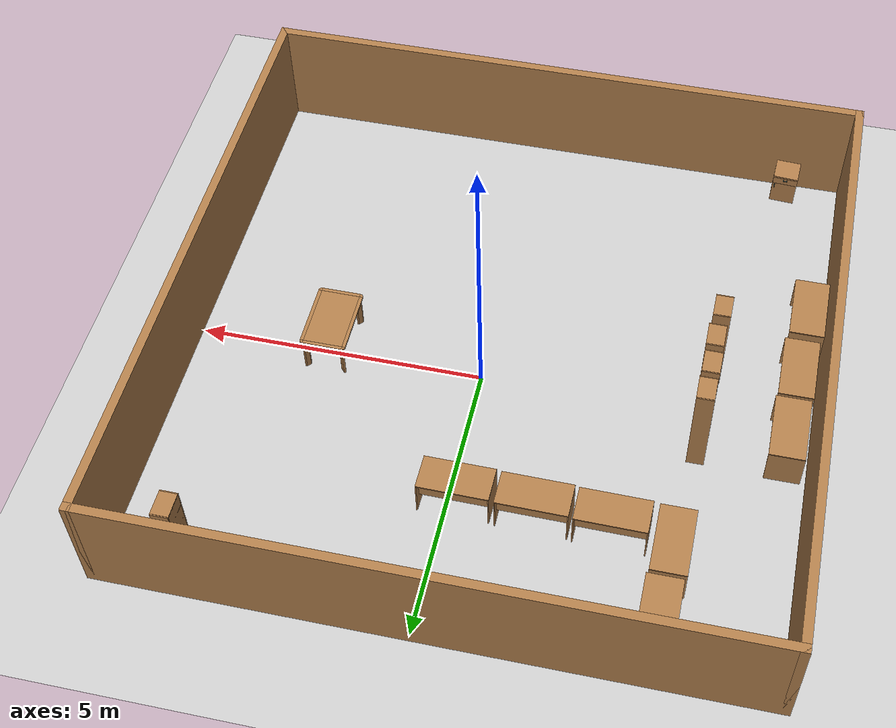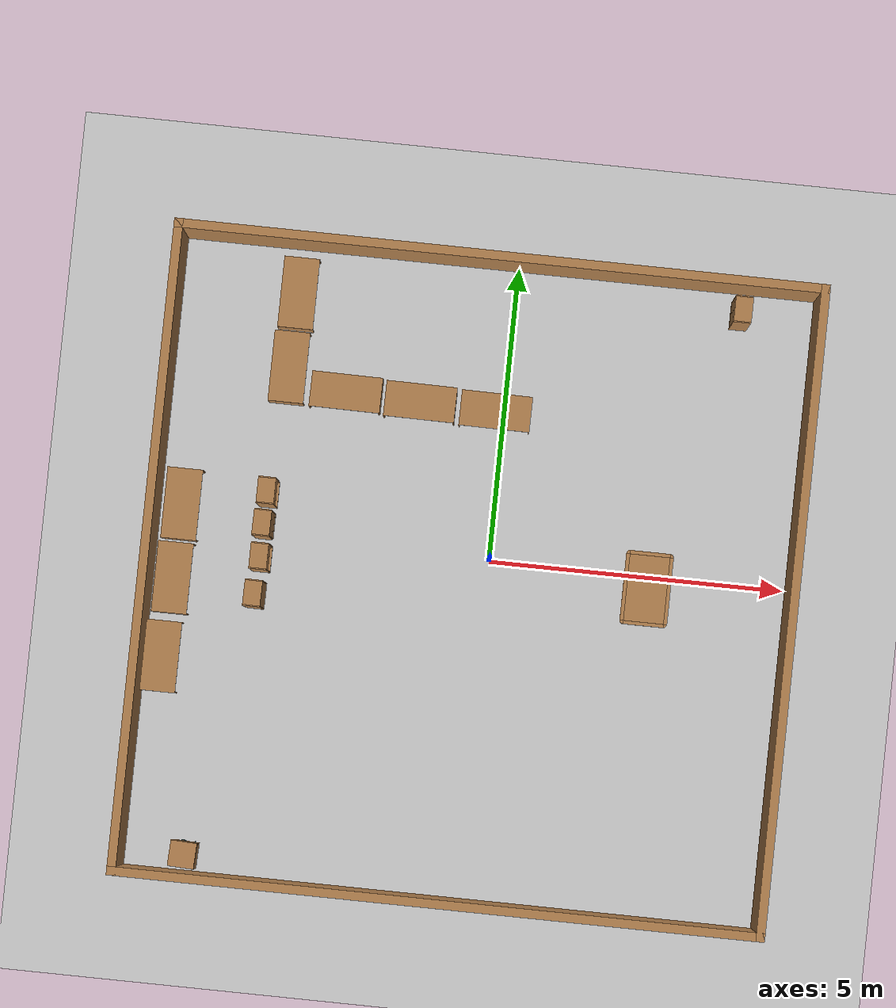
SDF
<sdf version="1.7">
 <world name="default">
  <light name="sun" type="directional">
   <pose>0 0 10 0 -0 0</pose>
   <diffuse>0.8 0.8 0.8 1</diffuse>
   <specular>0.1 0.1 0.1 1</specular>
   <attenuation>
    <range>1000</range>
    <constant>0.9</constant>
    <linear>0.01</linear>
    <quadratic>0.001</quadratic>
   </attenuation>
   <direction>-0.5 0.5 -1</direction>
   <spot><inner_angle>0</inner_angle><outer_angle>0</outer_angle><falloff>0</falloff></spot>
  </light>
  <model name="ground_plane">
   <static>1</static>
   <link name="link">
    <collision name="collision">
     <geometry><plane><normal>0 0 1</normal><size>100 100</size></plane></geometry>
     <surface><friction><ode><mu>100</mu><mu2>50</mu2></ode></friction></surface>
    </collision>
    <visual name="visual">
     <cast_shadows>0</cast_shadows>
     <geometry><plane><normal>0 0 1</normal><size>100 100</size></plane></geometry>
     <material>
      <script><uri>file://media/materials/scripts/gazebo.material</uri><name>Gazebo/Grey</name></script>
     </material>
    </visual>
   </link>
  </model>
  <gravity>0 0 -9.8</gravity>
  <magnetic_field>6e-06 2.3e-05 -4.2e-05</magnetic_field>
  <atmosphere type="adiabatic"/>
  <physics name="default_physics" default="0" type="ode">
   <max_step_size>0.001</max_step_size>
   <real_time_factor>1</real_time_factor>
   <real_time_update_rate>1000</real_time_update_rate>
  </physics>
  <scene><ambient>0.4 0.4 0.4 1</ambient><background>0.7 0.7 0.7 1</background><shadows>1</shadows></scene>
  <spherical_coordinates>
   <surface_model>EARTH_WGS84</surface_model>
   <latitude_deg>0</latitude_deg>
   <longitude_deg>0</longitude_deg>
   <elevation>0</elevation>
   <heading_deg>0</heading_deg>
  </spherical_coordinates>
  <model name="Untitled">
   <model name="Empty_World">
    <link name="Wall_6">
     <pose>0 5.425 0 0 -0 0</pose>
     <visual name="Wall_6_Visual">
      <pose>0 0 1 0 -0 0</pose>
      <geometry><box><size>11 0.15 2</size></box></geometry>
      <material>
       <script><uri>file://media/materials/scripts/gazebo.material</uri><name>Gazebo/Wood</name></script>
       <ambient>1 1 1 1</ambient>
       <diffuse>1 1 1 1</diffuse>
       <specular>0.2 0.2 0.2 1</specular>
       <emissive>0 0 0 1</emissive>
       <shader type="pixel"/>
      </material>
      <meta><layer>0</layer></meta>
     </visual>
     <collision name="Wall_6_Collision">
      <pose>0 0 1 0 -0 0</pose>
      <geometry><box><size>11 0.15 2</size></box></geometry>
      <surface>
       <friction>
        <ode><mu>1</mu><mu2>1</mu2><fdir1>0 0 0</fdir1><slip1>0</slip1><slip2>0</slip2></ode>
        <torsional>
         <coefficient>1</coefficient>
         <patch_radius>0</patch_radius>
         <surface_radius>0</surface_radius>
         <use_patch_radius>1</use_patch_radius>
         <ode><slip>0</slip></ode>
        </torsional>
       </friction>
       <bounce><restitution_coefficient>0</restitution_coefficient><threshold>1e+06</threshold></bounce>
       <contact>
        <collide_without_contact>0</collide_without_contact>
        <collide_without_contact_bitmask>1</collide_without_contact_bitmask>
        <collide_bitmask>1</collide_bitmask>
        <ode>
         <soft_cfm>0</soft_cfm>
         <soft_erp>0.2</soft_erp>
         <kp>1e+13</kp>
         <kd>1</kd>
         <max_vel>0.01</max_vel>
         <min_depth>0</min_depth>
        </ode>
        <bullet>
         <split_impulse>1</split_impulse>
         <split_impulse_penetration_threshold>-0.01</split_impulse_penetration_threshold>
         <soft_cfm>0</soft_cfm>
         <soft_erp>0.2</soft_erp>
         <kp>1e+13</kp>
         <kd>1</kd>
        </bullet>
       </contact>
      </surface>
     </collision>
    </link>
    <link name="Wall_7">
     <pose>5.425 0 0 0 0 -1.5708</pose>
     <visual name="Wall_7_Visual">
      <pose>0 0 1 0 -0 0</pose>
      <geometry><box><size>11 0.15 2</size></box></geometry>
      <material>
       <script><uri>file://media/materials/scripts/gazebo.material</uri><name>Gazebo/Wood</name></script>
       <ambient>1 1 1 1</ambient>
       <diffuse>1 1 1 1</diffuse>
       <specular>0.2 0.2 0.2 1</specular>
       <emissive>0 0 0 1</emissive>
       <shader type="pixel"/>
      </material>
      <meta><layer>0</layer></meta>
     </visual>
     <collision name="Wall_7_Collision">
      <pose>0 0 1 0 -0 0</pose>
      <geometry><box><size>11 0.15 2</size></box></geometry>
      <surface>
       <friction>
        <ode><mu>1</mu><mu2>1</mu2><fdir1>0 0 0</fdir1><slip1>0</slip1><slip2>0</slip2></ode>
        <torsional>
         <coefficient>1</coefficient>
         <patch_radius>0</patch_radius>
         <surface_radius>0</surface_radius>
         <use_patch_radius>1</use_patch_radius>
         <ode><slip>0</slip></ode>
        </torsional>
       </friction>
       <bounce><restitution_coefficient>0</restitution_coefficient><threshold>1e+06</threshold></bounce>
       <contact>
        <collide_without_contact>0</collide_without_contact>
        <collide_without_contact_bitmask>1</collide_without_contact_bitmask>
        <collide_bitmask>1</collide_bitmask>
        <ode>
         <soft_cfm>0</soft_cfm>
         <soft_erp>0.2</soft_erp>
         <kp>1e+13</kp>
         <kd>1</kd>
         <max_vel>0.01</max_vel>
         <min_depth>0</min_depth>
        </ode>
        <bullet>
         <split_impulse>1</split_impulse>
         <split_impulse_penetration_threshold>-0.01</split_impulse_penetration_threshold>
         <soft_cfm>0</soft_cfm>
         <soft_erp>0.2</soft_erp>
         <kp>1e+13</kp>
         <kd>1</kd>
        </bullet>
       </contact>
      </surface>
     </collision>
    </link>
    <link name="Wall_8">
     <pose>0 -5.425 0 0 -0 3.14159</pose>
     <visual name="Wall_8_Visual">
      <pose>0 0 1 0 -0 0</pose>
      <geometry><box><size>11 0.15 2</size></box></geometry>
      <material>
       <script><uri>file://media/materials/scripts/gazebo.material</uri><name>Gazebo/Wood</name></script>
       <ambient>1 1 1 1</ambient>
       <diffuse>1 1 1 1</diffuse>
       <specular>0.2 0.2 0.2 1</specular>
       <emissive>0 0 0 1</emissive>
       <shader type="pixel"/>
      </material>
      <meta><layer>0</layer></meta>
     </visual>
     <collision name="Wall_8_Collision">
      <pose>0 0 1 0 -0 0</pose>
      <geometry><box><size>11 0.15 2</size></box></geometry>
      <surface>
       <friction>
        <ode><mu>1</mu><mu2>1</mu2><fdir1>0 0 0</fdir1><slip1>0</slip1><slip2>0</slip2></ode>
        <torsional>
         <coefficient>1</coefficient>
         <patch_radius>0</patch_radius>
         <surface_radius>0</surface_radius>
         <use_patch_radius>1</use_patch_radius>
         <ode><slip>0</slip></ode>
        </torsional>
       </friction>
       <bounce><restitution_coefficient>0</restitution_coefficient><threshold>1e+06</threshold></bounce>
       <contact>
        <collide_without_contact>0</collide_without_contact>
        <collide_without_contact_bitmask>1</collide_without_contact_bitmask>
        <collide_bitmask>1</collide_bitmask>
        <ode>
         <soft_cfm>0</soft_cfm>
         <soft_erp>0.2</soft_erp>
         <kp>1e+13</kp>
         <kd>1</kd>
         <max_vel>0.01</max_vel>
         <min_depth>0</min_depth>
        </ode>
        <bullet>
         <split_impulse>1</split_impulse>
         <split_impulse_penetration_threshold>-0.01</split_impulse_penetration_threshold>
         <soft_cfm>0</soft_cfm>
         <soft_erp>0.2</soft_erp>
         <kp>1e+13</kp>
         <kd>1</kd>
        </bullet>
       </contact>
      </surface>
     </collision>
    </link>
    <link name="Wall_9">
     <pose>-5.425 0 0 0 -0 1.5708</pose>
     <visual name="Wall_9_Visual">
      <pose>0 0 1 0 -0 0</pose>
      <geometry><box><size>11 0.15 2</size></box></geometry>
      <material>
       <script><uri>file://media/materials/scripts/gazebo.material</uri><name>Gazebo/Wood</name></script>
       <ambient>1 1 1 1</ambient>
       <diffuse>1 1 1 1</diffuse>
       <specular>0.2 0.2 0.2 1</specular>
       <emissive>0 0 0 1</emissive>
       <shader type="pixel"/>
      </material>
      <meta><layer>0</layer></meta>
     </visual>
     <collision name="Wall_9_Collision">
      <pose>0 0 1 0 -0 0</pose>
      <geometry><box><size>11 0.15 2</size></box></geometry>
      <surface>
       <friction>
        <ode><mu>1</mu><mu2>1</mu2><fdir1>0 0 0</fdir1><slip1>0</slip1><slip2>0</slip2></ode>
        <torsional>
         <coefficient>1</coefficient>
         <patch_radius>0</patch_radius>
         <surface_radius>0</surface_radius>
         <use_patch_radius>1</use_patch_radius>
         <ode><slip>0</slip></ode>
        </torsional>
       </friction>
       <bounce><restitution_coefficient>0</restitution_coefficient><threshold>1e+06</threshold></bounce>
       <contact>
        <collide_without_contact>0</collide_without_contact>
        <collide_without_contact_bitmask>1</collide_without_contact_bitmask>
        <collide_bitmask>1</collide_bitmask>
        <ode>
         <soft_cfm>0</soft_cfm>
         <soft_erp>0.2</soft_erp>
         <kp>1e+13</kp>
         <kd>1</kd>
         <max_vel>0.01</max_vel>
         <min_depth>0</min_depth>
        </ode>
        <bullet>
         <split_impulse>1</split_impulse>
         <split_impulse_penetration_threshold>-0.01</split_impulse_penetration_threshold>
         <soft_cfm>0</soft_cfm>
         <soft_erp>0.2</soft_erp>
         <kp>1e+13</kp>
         <kd>1</kd>
        </bullet>
       </contact>
      </surface>
     </collision>
    </link>
    <static>1</static>
   </model>
   <static>0</static>
   <pose>-0.312257 -0.39044 0 0 -0 0</pose>
  </model>
  <model name="office_desk">
   <link name="link">
    <inertial>
     <mass>10</mass>
     <inertia><ixx>1</ixx><ixy>0</ixy><ixz>0</ixz><iyy>1</iyy><iyz>0</iyz><izz>1</izz></inertia>
    </inertial>
    <visual name="top_board">
     <pose>-0.3 0.6 0.69 0 -0 0</pose>
     <geometry><box><size>0.6 1.2 0.02</size></box></geometry>
     <material>
      <script>
       <uri>model://base_materials/wood/scripts/wood.material</uri>
       <name>base_materials/dark_wood</name>
      </script>
     </material>
    </visual>
    <collision name="collision_top_board">
     <pose>-0.3 0.6 0.69 0 -0 0</pose>
     <geometry><box><size>0.6 1.2 0.02</size></box></geometry>
    </collision>
    <visual name="left_board">
     <pose>-0.3 0.01 0.34 0 -0 0</pose>
     <geometry><box><size>0.6 0.02 0.68</size></box></geometry>
     <material>
      <script>
       <uri>model://base_materials/wood/scripts/wood.material</uri>
       <name>base_materials/dark_wood</name>
      </script>
     </material>
    </visual>
    <collision name="collision_left_board">
     <pose>-0.3 0.01 0.34 0 -0 0</pose>
     <geometry><box><size>0.6 0.02 0.68</size></box></geometry>
    </collision>
    <visual name="right_board">
     <pose>-0.3 1.19 0.34 0 -0 0</pose>
     <geometry><box><size>0.6 0.02 0.68</size></box></geometry>
     <material>
      <script>
       <uri>model://base_materials/wood/scripts/wood.material</uri>
       <name>base_materials/dark_wood</name>
      </script>
     </material>
    </visual>
    <collision name="collision_right_board">
     <pose>-0.3 1.19 0.34 0 -0 0</pose>
     <geometry><box><size>0.6 0.02 0.68</size></box></geometry>
    </collision>
    <visual name="center_board">
     <pose>-0.14 0.6 0.49 0 -0 0</pose>
     <geometry><box><size>0.02 1.16 0.4</size></box></geometry>
     <material>
      <script>
       <uri>model://base_materials/wood/scripts/wood.material</uri>
       <name>base_materials/dark_wood</name>
      </script>
     </material>
    </visual>
    <collision name="ollision_center_board">
     <pose>-0.14 0.6 0.49 0 -0 0</pose>
     <geometry><box><size>0.02 1.16 0.4</size></box></geometry>
    </collision>
    <velocity_decay><linear>0</linear><angular>0</angular></velocity_decay>
   </link>
   <static>1</static>
   <pose>-3.41065 2.31343 0 0 -0 0</pose>
  </model>
  <model name="office_desk_clone">
   <link name="link">
    <inertial>
     <mass>10</mass>
     <inertia><ixx>1</ixx><ixy>0</ixy><ixz>0</ixz><iyy>1</iyy><iyz>0</iyz><izz>1</izz></inertia>
    </inertial>
    <visual name="top_board">
     <pose>-0.3 0.6 0.69 0 -0 0</pose>
     <geometry><box><size>0.6 1.2 0.02</size></box></geometry>
     <material>
      <script>
       <uri>model://base_materials/wood/scripts/wood.material</uri>
       <name>base_materials/dark_wood</name>
      </script>
     </material>
    </visual>
    <collision name="collision_top_board">
     <pose>-0.3 0.6 0.69 0 -0 0</pose>
     <geometry><box><size>0.6 1.2 0.02</size></box></geometry>
    </collision>
    <visual name="left_board">
     <pose>-0.3 0.01 0.34 0 -0 0</pose>
     <geometry><box><size>0.6 0.02 0.68</size></box></geometry>
     <material>
      <script>
       <uri>model://base_materials/wood/scripts/wood.material</uri>
       <name>base_materials/dark_wood</name>
      </script>
     </material>
    </visual>
    <collision name="collision_left_board">
     <pose>-0.3 0.01 0.34 0 -0 0</pose>
     <geometry><box><size>0.6 0.02 0.68</size></box></geometry>
    </collision>
    <visual name="right_board">
     <pose>-0.3 1.19 0.34 0 -0 0</pose>
     <geometry><box><size>0.6 0.02 0.68</size></box></geometry>
     <material>
      <script>
       <uri>model://base_materials/wood/scripts/wood.material</uri>
       <name>base_materials/dark_wood</name>
      </script>
     </material>
    </visual>
    <collision name="collision_right_board">
     <pose>-0.3 1.19 0.34 0 -0 0</pose>
     <geometry><box><size>0.6 0.02 0.68</size></box></geometry>
    </collision>
    <visual name="center_board">
     <pose>-0.14 0.6 0.49 0 -0 0</pose>
     <geometry><box><size>0.02 1.16 0.4</size></box></geometry>
     <material>
      <script>
       <uri>model://base_materials/wood/scripts/wood.material</uri>
       <name>base_materials/dark_wood</name>
      </script>
     </material>
    </visual>
    <collision name="ollision_center_board">
     <pose>-0.14 0.6 0.49 0 -0 0</pose>
     <geometry><box><size>0.02 1.16 0.4</size></box></geometry>
    </collision>
    <velocity_decay><linear>0</linear><angular>0</angular></velocity_decay>
   </link>
   <static>1</static>
   <pose>-2.1081 2.88009 0 0 -0 1.56306</pose>
  </model>
  <model name="office_desk_clone_clone">
   <link name="link">
    <inertial>
     <mass>10</mass>
     <inertia><ixx>1</ixx><ixy>0</ixy><ixz>0</ixz><iyy>1</iyy><iyz>0</iyz><izz>1</izz></inertia>
    </inertial>
    <visual name="top_board">
     <pose>-0.3 0.6 0.69 0 -0 0</pose>
     <geometry><box><size>0.6 1.2 0.02</size></box></geometry>
     <material>
      <script>
       <uri>model://base_materials/wood/scripts/wood.material</uri>
       <name>base_materials/dark_wood</name>
      </script>
     </material>
    </visual>
    <collision name="collision_top_board">
     <pose>-0.3 0.6 0.69 0 -0 0</pose>
     <geometry><box><size>0.6 1.2 0.02</size></box></geometry>
    </collision>
    <visual name="left_board">
     <pose>-0.3 0.01 0.34 0 -0 0</pose>
     <geometry><box><size>0.6 0.02 0.68</size></box></geometry>
     <material>
      <script>
       <uri>model://base_materials/wood/scripts/wood.material</uri>
       <name>base_materials/dark_wood</name>
      </script>
     </material>
    </visual>
    <collision name="collision_left_board">
     <pose>-0.3 0.01 0.34 0 -0 0</pose>
     <geometry><box><size>0.6 0.02 0.68</size></box></geometry>
    </collision>
    <visual name="right_board">
     <pose>-0.3 1.19 0.34 0 -0 0</pose>
     <geometry><box><size>0.6 0.02 0.68</size></box></geometry>
     <material>
      <script>
       <uri>model://base_materials/wood/scripts/wood.material</uri>
       <name>base_materials/dark_wood</name>
      </script>
     </material>
    </visual>
    <collision name="collision_right_board">
     <pose>-0.3 1.19 0.34 0 -0 0</pose>
     <geometry><box><size>0.6 0.02 0.68</size></box></geometry>
    </collision>
    <visual name="center_board">
     <pose>-0.14 0.6 0.49 0 -0 0</pose>
     <geometry><box><size>0.02 1.16 0.4</size></box></geometry>
     <material>
      <script>
       <uri>model://base_materials/wood/scripts/wood.material</uri>
       <name>base_materials/dark_wood</name>
      </script>
     </material>
    </visual>
    <collision name="ollision_center_board">
     <pose>-0.14 0.6 0.49 0 -0 0</pose>
     <geometry><box><size>0.02 1.16 0.4</size></box></geometry>
    </collision>
    <velocity_decay><linear>0</linear><angular>0</angular></velocity_decay>
   </link>
   <static>1</static>
   <pose>-3.37655 3.57266 0 0 -0 0</pose>
  </model>
  <model name="office_desk_clone_clone_0">
   <link name="link">
    <inertial>
     <mass>10</mass>
     <inertia><ixx>1</ixx><ixy>0</ixy><ixz>0</ixz><iyy>1</iyy><iyz>0</iyz><izz>1</izz></inertia>
    </inertial>
    <visual name="top_board">
     <pose>-0.3 0.6 0.69 0 -0 0</pose>
     <geometry><box><size>0.6 1.2 0.02</size></box></geometry>
     <material>
      <script>
       <uri>model://base_materials/wood/scripts/wood.material</uri>
       <name>base_materials/dark_wood</name>
      </script>
     </material>
    </visual>
    <collision name="collision_top_board">
     <pose>-0.3 0.6 0.69 0 -0 0</pose>
     <geometry><box><size>0.6 1.2 0.02</size></box></geometry>
    </collision>
    <visual name="left_board">
     <pose>-0.3 0.01 0.34 0 -0 0</pose>
     <geometry><box><size>0.6 0.02 0.68</size></box></geometry>
     <material>
      <script>
       <uri>model://base_materials/wood/scripts/wood.material</uri>
       <name>base_materials/dark_wood</name>
      </script>
     </material>
    </visual>
    <collision name="collision_left_board">
     <pose>-0.3 0.01 0.34 0 -0 0</pose>
     <geometry><box><size>0.6 0.02 0.68</size></box></geometry>
    </collision>
    <visual name="right_board">
     <pose>-0.3 1.19 0.34 0 -0 0</pose>
     <geometry><box><size>0.6 0.02 0.68</size></box></geometry>
     <material>
      <script>
       <uri>model://base_materials/wood/scripts/wood.material</uri>
       <name>base_materials/dark_wood</name>
      </script>
     </material>
    </visual>
    <collision name="collision_right_board">
     <pose>-0.3 1.19 0.34 0 -0 0</pose>
     <geometry><box><size>0.6 0.02 0.68</size></box></geometry>
    </collision>
    <visual name="center_board">
     <pose>-0.14 0.6 0.49 0 -0 0</pose>
     <geometry><box><size>0.02 1.16 0.4</size></box></geometry>
     <material>
      <script>
       <uri>model://base_materials/wood/scripts/wood.material</uri>
       <name>base_materials/dark_wood</name>
      </script>
     </material>
    </visual>
    <collision name="ollision_center_board">
     <pose>-0.14 0.6 0.49 0 -0 0</pose>
     <geometry><box><size>0.02 1.16 0.4</size></box></geometry>
    </collision>
    <velocity_decay><linear>0</linear><angular>0</angular></velocity_decay>
   </link>
   <static>1</static>
   <pose>-0.839795 2.84629 0 0 -0 1.56306</pose>
  </model>
  <model name="office_desk_clone_clone_1">
   <link name="link">
    <inertial>
     <mass>10</mass>
     <inertia><ixx>1</ixx><ixy>0</ixy><ixz>0</ixz><iyy>1</iyy><iyz>0</iyz><izz>1</izz></inertia>
    </inertial>
    <visual name="top_board">
     <pose>-0.3 0.6 0.69 0 -0 0</pose>
     <geometry><box><size>0.6 1.2 0.02</size></box></geometry>
     <material>
      <script>
       <uri>model://base_materials/wood/scripts/wood.material</uri>
       <name>base_materials/dark_wood</name>
      </script>
     </material>
    </visual>
    <collision name="collision_top_board">
     <pose>-0.3 0.6 0.69 0 -0 0</pose>
     <geometry><box><size>0.6 1.2 0.02</size></box></geometry>
    </collision>
    <visual name="left_board">
     <pose>-0.3 0.01 0.34 0 -0 0</pose>
     <geometry><box><size>0.6 0.02 0.68</size></box></geometry>
     <material>
      <script>
       <uri>model://base_materials/wood/scripts/wood.material</uri>
       <name>base_materials/dark_wood</name>
      </script>
     </material>
    </visual>
    <collision name="collision_left_board">
     <pose>-0.3 0.01 0.34 0 -0 0</pose>
     <geometry><box><size>0.6 0.02 0.68</size></box></geometry>
    </collision>
    <visual name="right_board">
     <pose>-0.3 1.19 0.34 0 -0 0</pose>
     <geometry><box><size>0.6 0.02 0.68</size></box></geometry>
     <material>
      <script>
       <uri>model://base_materials/wood/scripts/wood.material</uri>
       <name>base_materials/dark_wood</name>
      </script>
     </material>
    </visual>
    <collision name="collision_right_board">
     <pose>-0.3 1.19 0.34 0 -0 0</pose>
     <geometry><box><size>0.6 0.02 0.68</size></box></geometry>
    </collision>
    <visual name="center_board">
     <pose>-0.14 0.6 0.49 0 -0 0</pose>
     <geometry><box><size>0.02 1.16 0.4</size></box></geometry>
     <material>
      <script>
       <uri>model://base_materials/wood/scripts/wood.material</uri>
       <name>base_materials/dark_wood</name>
      </script>
     </material>
    </visual>
    <collision name="ollision_center_board">
     <pose>-0.14 0.6 0.49 0 -0 0</pose>
     <geometry><box><size>0.02 1.16 0.4</size></box></geometry>
    </collision>
    <velocity_decay><linear>0</linear><angular>0</angular></velocity_decay>
   </link>
   <static>1</static>
   <pose>0.443376 2.81777 0 0 -0 1.56306</pose>
  </model>
  <model name="office_desk_clone_0">
   <link name="link">
    <inertial>
     <mass>10</mass>
     <inertia><ixx>1</ixx><ixy>0</ixy><ixz>0</ixz><iyy>1</iyy><iyz>0</iyz><izz>1</izz></inertia>
    </inertial>
    <visual name="top_board">
     <pose>-0.3 0.6 0.69 0 -0 0</pose>
     <geometry><box><size>0.6 1.2 0.02</size></box></geometry>
     <material>
      <script>
       <uri>model://base_materials/wood/scripts/wood.material</uri>
       <name>base_materials/dark_wood</name>
      </script>
     </material>
    </visual>
    <collision name="collision_top_board">
     <pose>-0.3 0.6 0.69 0 -0 0</pose>
     <geometry><box><size>0.6 1.2 0.02</size></box></geometry>
    </collision>
    <visual name="left_board">
     <pose>-0.3 0.01 0.34 0 -0 0</pose>
     <geometry><box><size>0.6 0.02 0.68</size></box></geometry>
     <material>
      <script>
       <uri>model://base_materials/wood/scripts/wood.material</uri>
       <name>base_materials/dark_wood</name>
      </script>
     </material>
    </visual>
    <collision name="collision_left_board">
     <pose>-0.3 0.01 0.34 0 -0 0</pose>
     <geometry><box><size>0.6 0.02 0.68</size></box></geometry>
    </collision>
    <visual name="right_board">
     <pose>-0.3 1.19 0.34 0 -0 0</pose>
     <geometry><box><size>0.6 0.02 0.68</size></box></geometry>
     <material>
      <script>
       <uri>model://base_materials/wood/scripts/wood.material</uri>
       <name>base_materials/dark_wood</name>
      </script>
     </material>
    </visual>
    <collision name="collision_right_board">
     <pose>-0.3 1.19 0.34 0 -0 0</pose>
     <geometry><box><size>0.6 0.02 0.68</size></box></geometry>
    </collision>
    <visual name="center_board">
     <pose>-0.14 0.6 0.49 0 -0 0</pose>
     <geometry><box><size>0.02 1.16 0.4</size></box></geometry>
     <material>
      <script>
       <uri>model://base_materials/wood/scripts/wood.material</uri>
       <name>base_materials/dark_wood</name>
      </script>
     </material>
    </visual>
    <collision name="ollision_center_board">
     <pose>-0.14 0.6 0.49 0 -0 0</pose>
     <geometry><box><size>0.02 1.16 0.4</size></box></geometry>
    </collision>
    <velocity_decay><linear>0</linear><angular>0</angular></velocity_decay>
   </link>
   <static>1</static>
   <pose>-4.97445 -0.175637 0 0 -0 0</pose>
  </model>
  <model name="office_desk_clone_1">
   <link name="link">
    <inertial>
     <mass>10</mass>
     <inertia><ixx>1</ixx><ixy>0</ixy><ixz>0</ixz><iyy>1</iyy><iyz>0</iyz><izz>1</izz></inertia>
    </inertial>
    <visual name="top_board">
     <pose>-0.3 0.6 0.69 0 -0 0</pose>
     <geometry><box><size>0.6 1.2 0.02</size></box></geometry>
     <material>
      <script>
       <uri>model://base_materials/wood/scripts/wood.material</uri>
       <name>base_materials/dark_wood</name>
      </script>
     </material>
    </visual>
    <collision name="collision_top_board">
     <pose>-0.3 0.6 0.69 0 -0 0</pose>
     <geometry><box><size>0.6 1.2 0.02</size></box></geometry>
    </collision>
    <visual name="left_board">
     <pose>-0.3 0.01 0.34 0 -0 0</pose>
     <geometry><box><size>0.6 0.02 0.68</size></box></geometry>
     <material>
      <script>
       <uri>model://base_materials/wood/scripts/wood.material</uri>
       <name>base_materials/dark_wood</name>
      </script>
     </material>
    </visual>
    <collision name="collision_left_board">
     <pose>-0.3 0.01 0.34 0 -0 0</pose>
     <geometry><box><size>0.6 0.02 0.68</size></box></geometry>
    </collision>
    <visual name="right_board">
     <pose>-0.3 1.19 0.34 0 -0 0</pose>
     <geometry><box><size>0.6 0.02 0.68</size></box></geometry>
     <material>
      <script>
       <uri>model://base_materials/wood/scripts/wood.material</uri>
       <name>base_materials/dark_wood</name>
      </script>
     </material>
    </visual>
    <collision name="collision_right_board">
     <pose>-0.3 1.19 0.34 0 -0 0</pose>
     <geometry><box><size>0.6 0.02 0.68</size></box></geometry>
    </collision>
    <visual name="center_board">
     <pose>-0.14 0.6 0.49 0 -0 0</pose>
     <geometry><box><size>0.02 1.16 0.4</size></box></geometry>
     <material>
      <script>
       <uri>model://base_materials/wood/scripts/wood.material</uri>
       <name>base_materials/dark_wood</name>
      </script>
     </material>
    </visual>
    <collision name="ollision_center_board">
     <pose>-0.14 0.6 0.49 0 -0 0</pose>
     <geometry><box><size>0.02 1.16 0.4</size></box></geometry>
    </collision>
    <velocity_decay><linear>0</linear><angular>0</angular></velocity_decay>
   </link>
   <static>1</static>
   <pose>-5.003 -1.43032 0 0 -0 0</pose>
  </model>
  <model name="office_desk_clone_2">
   <link name="link">
    <inertial>
     <mass>10</mass>
     <inertia><ixx>1</ixx><ixy>0</ixy><ixz>0</ixz><iyy>1</iyy><iyz>0</iyz><izz>1</izz></inertia>
    </inertial>
    <visual name="top_board">
     <pose>-0.3 0.6 0.69 0 -0 0</pose>
     <geometry><box><size>0.6 1.2 0.02</size></box></geometry>
     <material>
      <script>
       <uri>model://base_materials/wood/scripts/wood.material</uri>
       <name>base_materials/dark_wood</name>
      </script>
     </material>
    </visual>
    <collision name="collision_top_board">
     <pose>-0.3 0.6 0.69 0 -0 0</pose>
     <geometry><box><size>0.6 1.2 0.02</size></box></geometry>
    </collision>
    <visual name="left_board">
     <pose>-0.3 0.01 0.34 0 -0 0</pose>
     <geometry><box><size>0.6 0.02 0.68</size></box></geometry>
     <material>
      <script>
       <uri>model://base_materials/wood/scripts/wood.material</uri>
       <name>base_materials/dark_wood</name>
      </script>
     </material>
    </visual>
    <collision name="collision_left_board">
     <pose>-0.3 0.01 0.34 0 -0 0</pose>
     <geometry><box><size>0.6 0.02 0.68</size></box></geometry>
    </collision>
    <visual name="right_board">
     <pose>-0.3 1.19 0.34 0 -0 0</pose>
     <geometry><box><size>0.6 0.02 0.68</size></box></geometry>
     <material>
      <script>
       <uri>model://base_materials/wood/scripts/wood.material</uri>
       <name>base_materials/dark_wood</name>
      </script>
     </material>
    </visual>
    <collision name="collision_right_board">
     <pose>-0.3 1.19 0.34 0 -0 0</pose>
     <geometry><box><size>0.6 0.02 0.68</size></box></geometry>
    </collision>
    <visual name="center_board">
     <pose>-0.14 0.6 0.49 0 -0 0</pose>
     <geometry><box><size>0.02 1.16 0.4</size></box></geometry>
     <material>
      <script>
       <uri>model://base_materials/wood/scripts/wood.material</uri>
       <name>base_materials/dark_wood</name>
      </script>
     </material>
    </visual>
    <collision name="ollision_center_board">
     <pose>-0.14 0.6 0.49 0 -0 0</pose>
     <geometry><box><size>0.02 1.16 0.4</size></box></geometry>
    </collision>
    <velocity_decay><linear>0</linear><angular>0</angular></velocity_decay>
   </link>
   <static>1</static>
   <pose>-5.05966 -2.7706 0 0 -0 0</pose>
  </model>
  <model name="high_shelf">
   <link name="link">
    <inertial>
     <mass>5</mass>
     <inertia><ixx>1</ixx><ixy>0</ixy><ixz>0</ixz><iyy>1</iyy><iyz>0</iyz><izz>1</izz></inertia>
    </inertial>
    <visual name="left_board">
     <pose>-0.1475 0.009 0.898 0 -0 0</pose>
     <geometry><box><size>0.295 0.018 1.796</size></box></geometry>
     <material>
      <script>
       <uri>model://base_materials/wood/scripts</uri>
       <uri>model://base_materials/wood/textures</uri>
       <name>base_materials/light_wood</name>
      </script>
     </material>
    </visual>
    <collision name="collision_left_board">
     <pose>-0.1475 0.009 0.898 0 -0 0</pose>
     <geometry><box><size>0.295 0.018 1.796</size></box></geometry>
    </collision>
    <visual name="right_board">
     <pose>-0.1475 0.441 0.898 0 -0 0</pose>
     <geometry><box><size>0.295 0.018 1.796</size></box></geometry>
     <material>
      <script>
       <uri>model://base_materials/wood/scripts</uri>
       <uri>model://base_materials/wood/textures</uri>
       <name>base_materials/light_wood</name>
      </script>
     </material>
    </visual>
    <collision name="collision_right_board">
     <pose>-0.1475 0.441 0.898 0 -0 0</pose>
     <geometry><box><size>0.295 0.018 1.796</size></box></geometry>
    </collision>
    <visual name="top_board">
     <pose>-0.1475 0.225 1.7825 0 -0 0</pose>
     <geometry><box><size>0.295 0.414 0.035</size></box></geometry>
     <material>
      <script>
       <uri>model://base_materials/wood/scripts</uri>
       <uri>model://base_materials/wood/textures</uri>
       <name>base_materials/light_wood</name>
      </script>
     </material>
    </visual>
    <collision name="collision_top_board">
     <pose>-0.1475 0.225 1.7825 0 -0 0</pose>
     <geometry><box><size>0.295 0.414 0.035</size></box></geometry>
    </collision>
    <visual name="1st_shelf">
     <pose>-0.162 0.225 1.51 0 -0 0</pose>
     <geometry><box><size>0.266 0.414 0.018</size></box></geometry>
     <material>
      <script>
       <uri>model://base_materials/wood/scripts</uri>
       <uri>model://base_materials/wood/textures</uri>
       <name>base_materials/light_wood</name>
      </script>
     </material>
    </visual>
    <collision name="collision_1st_shelf">
     <pose>-0.162 0.225 1.51 0 -0 0</pose>
     <geometry><box><size>0.266 0.414 0.018</size></box></geometry>
    </collision>
    <visual name="2nd_shelf">
     <pose>-0.162 0.225 1.22 0 -0 0</pose>
     <geometry><box><size>0.266 0.414 0.018</size></box></geometry>
     <material>
      <script>
       <uri>model://base_materials/wood/scripts</uri>
       <uri>model://base_materials/wood/textures</uri>
       <name>base_materials/light_wood</name>
      </script>
     </material>
    </visual>
    <collision name="collision_2nd_shelf">
     <pose>-0.162 0.225 1.22 0 -0 0</pose>
     <geometry><box><size>0.266 0.414 0.018</size></box></geometry>
    </collision>
    <visual name="3rd_shelf">
     <pose>-0.162 0.225 0.93 0 -0 0</pose>
     <geometry><box><size>0.266 0.414 0.018</size></box></geometry>
     <material>
      <script>
       <uri>model://base_materials/wood/scripts</uri>
       <uri>model://base_materials/wood/textures</uri>
       <name>base_materials/light_wood</name>
      </script>
     </material>
    </visual>
    <collision name="collision_3rd_shelf">
     <pose>-0.162 0.225 0.93 0 -0 0</pose>
     <geometry><box><size>0.266 0.414 0.018</size></box></geometry>
    </collision>
    <visual name="4th_shelf">
     <pose>-0.162 0.225 0.65 0 -0 0</pose>
     <geometry><box><size>0.266 0.414 0.018</size></box></geometry>
     <material>
      <script>
       <uri>model://base_materials/wood/scripts</uri>
       <uri>model://base_materials/wood/textures</uri>
       <name>base_materials/light_wood</name>
      </script>
     </material>
    </visual>
    <collision name="collision_4th_shelf">
     <pose>-0.162 0.225 0.65 0 -0 0</pose>
     <geometry><box><size>0.266 0.414 0.018</size></box></geometry>
    </collision>
    <visual name="5th_shelf">
     <pose>-0.162 0.225 0.36 0 -0 0</pose>
     <geometry><box><size>0.266 0.414 0.018</size></box></geometry>
     <material>
      <script>
       <uri>model://base_materials/wood/scripts</uri>
       <uri>model://base_materials/wood/textures</uri>
       <name>base_materials/light_wood</name>
      </script>
     </material>
    </visual>
    <collision name="collision_5th_shelf">
     <pose>-0.162 0.225 0.36 0 -0 0</pose>
     <geometry><box><size>0.266 0.414 0.018</size></box></geometry>
    </collision>
    <visual name="bottom_board">
     <pose>-0.1475 0.225 0.035 0 -0 0</pose>
     <geometry><box><size>0.295 0.414 0.07</size></box></geometry>
     <material>
      <script>
       <uri>model://base_materials/wood/scripts</uri>
       <uri>model://base_materials/wood/textures</uri>
       <name>base_materials/light_wood</name>
      </script>
     </material>
    </visual>
    <collision name="collision_bottom_board">
     <pose>-0.1475 0.225 0.035 0 -0 0</pose>
     <geometry><box><size>0.295 0.414 0.07</size></box></geometry>
    </collision>
    <visual name="back_board">
     <pose>-0.286 0.225 0.898 0 -0 0</pose>
     <geometry><box><size>0.018 0.414 1.796</size></box></geometry>
     <material>
      <script>
       <uri>model://base_materials/wood/scripts</uri>
       <uri>model://base_materials/wood/textures</uri>
       <name>base_materials/light_wood</name>
      </script>
     </material>
    </visual>
    <collision name="collision_back_board">
     <pose>-0.286 0.225 0.898 0 -0 0</pose>
     <geometry><box><size>0.018 0.414 1.796</size></box></geometry>
    </collision>
    <velocity_decay><linear>0</linear><angular>0</angular></velocity_decay>
   </link>
   <static>1</static>
   <pose>-3.68843 0.528349 0 0 -0 0</pose>
  </model>
  <model name="high_shelf_clone">
   <link name="link">
    <inertial>
     <mass>5</mass>
     <inertia><ixx>1</ixx><ixy>0</ixy><ixz>0</ixz><iyy>1</iyy><iyz>0</iyz><izz>1</izz></inertia>
    </inertial>
    <visual name="left_board">
     <pose>-0.1475 0.009 0.898 0 -0 0</pose>
     <geometry><box><size>0.295 0.018 1.796</size></box></geometry>
     <material>
      <script>
       <uri>model://base_materials/wood/scripts</uri>
       <uri>model://base_materials/wood/textures</uri>
       <name>base_materials/light_wood</name>
      </script>
     </material>
    </visual>
    <collision name="collision_left_board">
     <pose>-0.1475 0.009 0.898 0 -0 0</pose>
     <geometry><box><size>0.295 0.018 1.796</size></box></geometry>
    </collision>
    <visual name="right_board">
     <pose>-0.1475 0.441 0.898 0 -0 0</pose>
     <geometry><box><size>0.295 0.018 1.796</size></box></geometry>
     <material>
      <script>
       <uri>model://base_materials/wood/scripts</uri>
       <uri>model://base_materials/wood/textures</uri>
       <name>base_materials/light_wood</name>
      </script>
     </material>
    </visual>
    <collision name="collision_right_board">
     <pose>-0.1475 0.441 0.898 0 -0 0</pose>
     <geometry><box><size>0.295 0.018 1.796</size></box></geometry>
    </collision>
    <visual name="top_board">
     <pose>-0.1475 0.225 1.7825 0 -0 0</pose>
     <geometry><box><size>0.295 0.414 0.035</size></box></geometry>
     <material>
      <script>
       <uri>model://base_materials/wood/scripts</uri>
       <uri>model://base_materials/wood/textures</uri>
       <name>base_materials/light_wood</name>
      </script>
     </material>
    </visual>
    <collision name="collision_top_board">
     <pose>-0.1475 0.225 1.7825 0 -0 0</pose>
     <geometry><box><size>0.295 0.414 0.035</size></box></geometry>
    </collision>
    <visual name="1st_shelf">
     <pose>-0.162 0.225 1.51 0 -0 0</pose>
     <geometry><box><size>0.266 0.414 0.018</size></box></geometry>
     <material>
      <script>
       <uri>model://base_materials/wood/scripts</uri>
       <uri>model://base_materials/wood/textures</uri>
       <name>base_materials/light_wood</name>
      </script>
     </material>
    </visual>
    <collision name="collision_1st_shelf">
     <pose>-0.162 0.225 1.51 0 -0 0</pose>
     <geometry><box><size>0.266 0.414 0.018</size></box></geometry>
    </collision>
    <visual name="2nd_shelf">
     <pose>-0.162 0.225 1.22 0 -0 0</pose>
     <geometry><box><size>0.266 0.414 0.018</size></box></geometry>
     <material>
      <script>
       <uri>model://base_materials/wood/scripts</uri>
       <uri>model://base_materials/wood/textures</uri>
       <name>base_materials/light_wood</name>
      </script>
     </material>
    </visual>
    <collision name="collision_2nd_shelf">
     <pose>-0.162 0.225 1.22 0 -0 0</pose>
     <geometry><box><size>0.266 0.414 0.018</size></box></geometry>
    </collision>
    <visual name="3rd_shelf">
     <pose>-0.162 0.225 0.93 0 -0 0</pose>
     <geometry><box><size>0.266 0.414 0.018</size></box></geometry>
     <material>
      <script>
       <uri>model://base_materials/wood/scripts</uri>
       <uri>model://base_materials/wood/textures</uri>
       <name>base_materials/light_wood</name>
      </script>
     </material>
    </visual>
    <collision name="collision_3rd_shelf">
     <pose>-0.162 0.225 0.93 0 -0 0</pose>
     <geometry><box><size>0.266 0.414 0.018</size></box></geometry>
    </collision>
    <visual name="4th_shelf">
     <pose>-0.162 0.225 0.65 0 -0 0</pose>
     <geometry><box><size>0.266 0.414 0.018</size></box></geometry>
     <material>
      <script>
       <uri>model://base_materials/wood/scripts</uri>
       <uri>model://base_materials/wood/textures</uri>
       <name>base_materials/light_wood</name>
      </script>
     </material>
    </visual>
    <collision name="collision_4th_shelf">
     <pose>-0.162 0.225 0.65 0 -0 0</pose>
     <geometry><box><size>0.266 0.414 0.018</size></box></geometry>
    </collision>
    <visual name="5th_shelf">
     <pose>-0.162 0.225 0.36 0 -0 0</pose>
     <geometry><box><size>0.266 0.414 0.018</size></box></geometry>
     <material>
      <script>
       <uri>model://base_materials/wood/scripts</uri>
       <uri>model://base_materials/wood/textures</uri>
       <name>base_materials/light_wood</name>
      </script>
     </material>
    </visual>
    <collision name="collision_5th_shelf">
     <pose>-0.162 0.225 0.36 0 -0 0</pose>
     <geometry><box><size>0.266 0.414 0.018</size></box></geometry>
    </collision>
    <visual name="bottom_board">
     <pose>-0.1475 0.225 0.035 0 -0 0</pose>
     <geometry><box><size>0.295 0.414 0.07</size></box></geometry>
     <material>
      <script>
       <uri>model://base_materials/wood/scripts</uri>
       <uri>model://base_materials/wood/textures</uri>
       <name>base_materials/light_wood</name>
      </script>
     </material>
    </visual>
    <collision name="collision_bottom_board">
     <pose>-0.1475 0.225 0.035 0 -0 0</pose>
     <geometry><box><size>0.295 0.414 0.07</size></box></geometry>
    </collision>
    <visual name="back_board">
     <pose>-0.286 0.225 0.898 0 -0 0</pose>
     <geometry><box><size>0.018 0.414 1.796</size></box></geometry>
     <material>
      <script>
       <uri>model://base_materials/wood/scripts</uri>
       <uri>model://base_materials/wood/textures</uri>
       <name>base_materials/light_wood</name>
      </script>
     </material>
    </visual>
    <collision name="collision_back_board">
     <pose>-0.286 0.225 0.898 0 -0 0</pose>
     <geometry><box><size>0.018 0.414 1.796</size></box></geometry>
    </collision>
    <velocity_decay><linear>0</linear><angular>0</angular></velocity_decay>
   </link>
   <static>1</static>
   <pose>-3.99579 0.437995 0 0 -0 3.13126</pose>
  </model>
  <model name="high_shelf_clone_0">
   <link name="link">
    <inertial>
     <mass>5</mass>
     <inertia><ixx>1</ixx><ixy>0</ixy><ixz>0</ixz><iyy>1</iyy><iyz>0</iyz><izz>1</izz></inertia>
    </inertial>
    <visual name="left_board">
     <pose>-0.1475 0.009 0.898 0 -0 0</pose>
     <geometry><box><size>0.295 0.018 1.796</size></box></geometry>
     <material>
      <script>
       <uri>model://base_materials/wood/scripts</uri>
       <uri>model://base_materials/wood/textures</uri>
       <name>base_materials/light_wood</name>
      </script>
     </material>
    </visual>
    <collision name="collision_left_board">
     <pose>-0.1475 0.009 0.898 0 -0 0</pose>
     <geometry><box><size>0.295 0.018 1.796</size></box></geometry>
    </collision>
    <visual name="right_board">
     <pose>-0.1475 0.441 0.898 0 -0 0</pose>
     <geometry><box><size>0.295 0.018 1.796</size></box></geometry>
     <material>
      <script>
       <uri>model://base_materials/wood/scripts</uri>
       <uri>model://base_materials/wood/textures</uri>
       <name>base_materials/light_wood</name>
      </script>
     </material>
    </visual>
    <collision name="collision_right_board">
     <pose>-0.1475 0.441 0.898 0 -0 0</pose>
     <geometry><box><size>0.295 0.018 1.796</size></box></geometry>
    </collision>
    <visual name="top_board">
     <pose>-0.1475 0.225 1.7825 0 -0 0</pose>
     <geometry><box><size>0.295 0.414 0.035</size></box></geometry>
     <material>
      <script>
       <uri>model://base_materials/wood/scripts</uri>
       <uri>model://base_materials/wood/textures</uri>
       <name>base_materials/light_wood</name>
      </script>
     </material>
    </visual>
    <collision name="collision_top_board">
     <pose>-0.1475 0.225 1.7825 0 -0 0</pose>
     <geometry><box><size>0.295 0.414 0.035</size></box></geometry>
    </collision>
    <visual name="1st_shelf">
     <pose>-0.162 0.225 1.51 0 -0 0</pose>
     <geometry><box><size>0.266 0.414 0.018</size></box></geometry>
     <material>
      <script>
       <uri>model://base_materials/wood/scripts</uri>
       <uri>model://base_materials/wood/textures</uri>
       <name>base_materials/light_wood</name>
      </script>
     </material>
    </visual>
    <collision name="collision_1st_shelf">
     <pose>-0.162 0.225 1.51 0 -0 0</pose>
     <geometry><box><size>0.266 0.414 0.018</size></box></geometry>
    </collision>
    <visual name="2nd_shelf">
     <pose>-0.162 0.225 1.22 0 -0 0</pose>
     <geometry><box><size>0.266 0.414 0.018</size></box></geometry>
     <material>
      <script>
       <uri>model://base_materials/wood/scripts</uri>
       <uri>model://base_materials/wood/textures</uri>
       <name>base_materials/light_wood</name>
      </script>
     </material>
    </visual>
    <collision name="collision_2nd_shelf">
     <pose>-0.162 0.225 1.22 0 -0 0</pose>
     <geometry><box><size>0.266 0.414 0.018</size></box></geometry>
    </collision>
    <visual name="3rd_shelf">
     <pose>-0.162 0.225 0.93 0 -0 0</pose>
     <geometry><box><size>0.266 0.414 0.018</size></box></geometry>
     <material>
      <script>
       <uri>model://base_materials/wood/scripts</uri>
       <uri>model://base_materials/wood/textures</uri>
       <name>base_materials/light_wood</name>
      </script>
     </material>
    </visual>
    <collision name="collision_3rd_shelf">
     <pose>-0.162 0.225 0.93 0 -0 0</pose>
     <geometry><box><size>0.266 0.414 0.018</size></box></geometry>
    </collision>
    <visual name="4th_shelf">
     <pose>-0.162 0.225 0.65 0 -0 0</pose>
     <geometry><box><size>0.266 0.414 0.018</size></box></geometry>
     <material>
      <script>
       <uri>model://base_materials/wood/scripts</uri>
       <uri>model://base_materials/wood/textures</uri>
       <name>base_materials/light_wood</name>
      </script>
     </material>
    </visual>
    <collision name="collision_4th_shelf">
     <pose>-0.162 0.225 0.65 0 -0 0</pose>
     <geometry><box><size>0.266 0.414 0.018</size></box></geometry>
    </collision>
    <visual name="5th_shelf">
     <pose>-0.162 0.225 0.36 0 -0 0</pose>
     <geometry><box><size>0.266 0.414 0.018</size></box></geometry>
     <material>
      <script>
       <uri>model://base_materials/wood/scripts</uri>
       <uri>model://base_materials/wood/textures</uri>
       <name>base_materials/light_wood</name>
      </script>
     </material>
    </visual>
    <collision name="collision_5th_shelf">
     <pose>-0.162 0.225 0.36 0 -0 0</pose>
     <geometry><box><size>0.266 0.414 0.018</size></box></geometry>
    </collision>
    <visual name="bottom_board">
     <pose>-0.1475 0.225 0.035 0 -0 0</pose>
     <geometry><box><size>0.295 0.414 0.07</size></box></geometry>
     <material>
      <script>
       <uri>model://base_materials/wood/scripts</uri>
       <uri>model://base_materials/wood/textures</uri>
       <name>base_materials/light_wood</name>
      </script>
     </material>
    </visual>
    <collision name="collision_bottom_board">
     <pose>-0.1475 0.225 0.035 0 -0 0</pose>
     <geometry><box><size>0.295 0.414 0.07</size></box></geometry>
    </collision>
    <visual name="back_board">
     <pose>-0.286 0.225 0.898 0 -0 0</pose>
     <geometry><box><size>0.018 0.414 1.796</size></box></geometry>
     <material>
      <script>
       <uri>model://base_materials/wood/scripts</uri>
       <uri>model://base_materials/wood/textures</uri>
       <name>base_materials/light_wood</name>
      </script>
     </material>
    </visual>
    <collision name="collision_back_board">
     <pose>-0.286 0.225 0.898 0 -0 0</pose>
     <geometry><box><size>0.018 0.414 1.796</size></box></geometry>
    </collision>
    <velocity_decay><linear>0</linear><angular>0</angular></velocity_decay>
   </link>
   <static>1</static>
   <pose>-3.69673 -0.57353 0 0 -0 0</pose>
  </model>
  <model name="high_shelf_clone_clone">
   <link name="link">
    <inertial>
     <mass>5</mass>
     <inertia><ixx>1</ixx><ixy>0</ixy><ixz>0</ixz><iyy>1</iyy><iyz>0</iyz><izz>1</izz></inertia>
    </inertial>
    <visual name="left_board">
     <pose>-0.1475 0.009 0.898 0 -0 0</pose>
     <geometry><box><size>0.295 0.018 1.796</size></box></geometry>
     <material>
      <script>
       <uri>model://base_materials/wood/scripts</uri>
       <uri>model://base_materials/wood/textures</uri>
       <name>base_materials/light_wood</name>
      </script>
     </material>
    </visual>
    <collision name="collision_left_board">
     <pose>-0.1475 0.009 0.898 0 -0 0</pose>
     <geometry><box><size>0.295 0.018 1.796</size></box></geometry>
    </collision>
    <visual name="right_board">
     <pose>-0.1475 0.441 0.898 0 -0 0</pose>
     <geometry><box><size>0.295 0.018 1.796</size></box></geometry>
     <material>
      <script>
       <uri>model://base_materials/wood/scripts</uri>
       <uri>model://base_materials/wood/textures</uri>
       <name>base_materials/light_wood</name>
      </script>
     </material>
    </visual>
    <collision name="collision_right_board">
     <pose>-0.1475 0.441 0.898 0 -0 0</pose>
     <geometry><box><size>0.295 0.018 1.796</size></box></geometry>
    </collision>
    <visual name="top_board">
     <pose>-0.1475 0.225 1.7825 0 -0 0</pose>
     <geometry><box><size>0.295 0.414 0.035</size></box></geometry>
     <material>
      <script>
       <uri>model://base_materials/wood/scripts</uri>
       <uri>model://base_materials/wood/textures</uri>
       <name>base_materials/light_wood</name>
      </script>
     </material>
    </visual>
    <collision name="collision_top_board">
     <pose>-0.1475 0.225 1.7825 0 -0 0</pose>
     <geometry><box><size>0.295 0.414 0.035</size></box></geometry>
    </collision>
    <visual name="1st_shelf">
     <pose>-0.162 0.225 1.51 0 -0 0</pose>
     <geometry><box><size>0.266 0.414 0.018</size></box></geometry>
     <material>
      <script>
       <uri>model://base_materials/wood/scripts</uri>
       <uri>model://base_materials/wood/textures</uri>
       <name>base_materials/light_wood</name>
      </script>
     </material>
    </visual>
    <collision name="collision_1st_shelf">
     <pose>-0.162 0.225 1.51 0 -0 0</pose>
     <geometry><box><size>0.266 0.414 0.018</size></box></geometry>
    </collision>
    <visual name="2nd_shelf">
     <pose>-0.162 0.225 1.22 0 -0 0</pose>
     <geometry><box><size>0.266 0.414 0.018</size></box></geometry>
     <material>
      <script>
       <uri>model://base_materials/wood/scripts</uri>
       <uri>model://base_materials/wood/textures</uri>
       <name>base_materials/light_wood</name>
      </script>
     </material>
    </visual>
    <collision name="collision_2nd_shelf">
     <pose>-0.162 0.225 1.22 0 -0 0</pose>
     <geometry><box><size>0.266 0.414 0.018</size></box></geometry>
    </collision>
    <visual name="3rd_shelf">
     <pose>-0.162 0.225 0.93 0 -0 0</pose>
     <geometry><box><size>0.266 0.414 0.018</size></box></geometry>
     <material>
      <script>
       <uri>model://base_materials/wood/scripts</uri>
       <uri>model://base_materials/wood/textures</uri>
       <name>base_materials/light_wood</name>
      </script>
     </material>
    </visual>
    <collision name="collision_3rd_shelf">
     <pose>-0.162 0.225 0.93 0 -0 0</pose>
     <geometry><box><size>0.266 0.414 0.018</size></box></geometry>
    </collision>
    <visual name="4th_shelf">
     <pose>-0.162 0.225 0.65 0 -0 0</pose>
     <geometry><box><size>0.266 0.414 0.018</size></box></geometry>
     <material>
      <script>
       <uri>model://base_materials/wood/scripts</uri>
       <uri>model://base_materials/wood/textures</uri>
       <name>base_materials/light_wood</name>
      </script>
     </material>
    </visual>
    <collision name="collision_4th_shelf">
     <pose>-0.162 0.225 0.65 0 -0 0</pose>
     <geometry><box><size>0.266 0.414 0.018</size></box></geometry>
    </collision>
    <visual name="5th_shelf">
     <pose>-0.162 0.225 0.36 0 -0 0</pose>
     <geometry><box><size>0.266 0.414 0.018</size></box></geometry>
     <material>
      <script>
       <uri>model://base_materials/wood/scripts</uri>
       <uri>model://base_materials/wood/textures</uri>
       <name>base_materials/light_wood</name>
      </script>
     </material>
    </visual>
    <collision name="collision_5th_shelf">
     <pose>-0.162 0.225 0.36 0 -0 0</pose>
     <geometry><box><size>0.266 0.414 0.018</size></box></geometry>
    </collision>
    <visual name="bottom_board">
     <pose>-0.1475 0.225 0.035 0 -0 0</pose>
     <geometry><box><size>0.295 0.414 0.07</size></box></geometry>
     <material>
      <script>
       <uri>model://base_materials/wood/scripts</uri>
       <uri>model://base_materials/wood/textures</uri>
       <name>base_materials/light_wood</name>
      </script>
     </material>
    </visual>
    <collision name="collision_bottom_board">
     <pose>-0.1475 0.225 0.035 0 -0 0</pose>
     <geometry><box><size>0.295 0.414 0.07</size></box></geometry>
    </collision>
    <visual name="back_board">
     <pose>-0.286 0.225 0.898 0 -0 0</pose>
     <geometry><box><size>0.018 0.414 1.796</size></box></geometry>
     <material>
      <script>
       <uri>model://base_materials/wood/scripts</uri>
       <uri>model://base_materials/wood/textures</uri>
       <name>base_materials/light_wood</name>
      </script>
     </material>
    </visual>
    <collision name="collision_back_board">
     <pose>-0.286 0.225 0.898 0 -0 0</pose>
     <geometry><box><size>0.018 0.414 1.796</size></box></geometry>
    </collision>
    <velocity_decay><linear>0</linear><angular>0</angular></velocity_decay>
   </link>
   <static>1</static>
   <pose>-4.02785 -0.749438 0 0 -0 3.13126</pose>
  </model>
  <model name="high_shelf_clone_clone_0">
   <link name="link">
    <inertial>
     <mass>5</mass>
     <inertia><ixx>1</ixx><ixy>0</ixy><ixz>0</ixz><iyy>1</iyy><iyz>0</iyz><izz>1</izz></inertia>
    </inertial>
    <visual name="left_board">
     <pose>-0.1475 0.009 0.898 0 -0 0</pose>
     <geometry><box><size>0.295 0.018 1.796</size></box></geometry>
     <material>
      <script>
       <uri>model://base_materials/wood/scripts</uri>
       <uri>model://base_materials/wood/textures</uri>
       <name>base_materials/light_wood</name>
      </script>
     </material>
    </visual>
    <collision name="collision_left_board">
     <pose>-0.1475 0.009 0.898 0 -0 0</pose>
     <geometry><box><size>0.295 0.018 1.796</size></box></geometry>
    </collision>
    <visual name="right_board">
     <pose>-0.1475 0.441 0.898 0 -0 0</pose>
     <geometry><box><size>0.295 0.018 1.796</size></box></geometry>
     <material>
      <script>
       <uri>model://base_materials/wood/scripts</uri>
       <uri>model://base_materials/wood/textures</uri>
       <name>base_materials/light_wood</name>
      </script>
     </material>
    </visual>
    <collision name="collision_right_board">
     <pose>-0.1475 0.441 0.898 0 -0 0</pose>
     <geometry><box><size>0.295 0.018 1.796</size></box></geometry>
    </collision>
    <visual name="top_board">
     <pose>-0.1475 0.225 1.7825 0 -0 0</pose>
     <geometry><box><size>0.295 0.414 0.035</size></box></geometry>
     <material>
      <script>
       <uri>model://base_materials/wood/scripts</uri>
       <uri>model://base_materials/wood/textures</uri>
       <name>base_materials/light_wood</name>
      </script>
     </material>
    </visual>
    <collision name="collision_top_board">
     <pose>-0.1475 0.225 1.7825 0 -0 0</pose>
     <geometry><box><size>0.295 0.414 0.035</size></box></geometry>
    </collision>
    <visual name="1st_shelf">
     <pose>-0.162 0.225 1.51 0 -0 0</pose>
     <geometry><box><size>0.266 0.414 0.018</size></box></geometry>
     <material>
      <script>
       <uri>model://base_materials/wood/scripts</uri>
       <uri>model://base_materials/wood/textures</uri>
       <name>base_materials/light_wood</name>
      </script>
     </material>
    </visual>
    <collision name="collision_1st_shelf">
     <pose>-0.162 0.225 1.51 0 -0 0</pose>
     <geometry><box><size>0.266 0.414 0.018</size></box></geometry>
    </collision>
    <visual name="2nd_shelf">
     <pose>-0.162 0.225 1.22 0 -0 0</pose>
     <geometry><box><size>0.266 0.414 0.018</size></box></geometry>
     <material>
      <script>
       <uri>model://base_materials/wood/scripts</uri>
       <uri>model://base_materials/wood/textures</uri>
       <name>base_materials/light_wood</name>
      </script>
     </material>
    </visual>
    <collision name="collision_2nd_shelf">
     <pose>-0.162 0.225 1.22 0 -0 0</pose>
     <geometry><box><size>0.266 0.414 0.018</size></box></geometry>
    </collision>
    <visual name="3rd_shelf">
     <pose>-0.162 0.225 0.93 0 -0 0</pose>
     <geometry><box><size>0.266 0.414 0.018</size></box></geometry>
     <material>
      <script>
       <uri>model://base_materials/wood/scripts</uri>
       <uri>model://base_materials/wood/textures</uri>
       <name>base_materials/light_wood</name>
      </script>
     </material>
    </visual>
    <collision name="collision_3rd_shelf">
     <pose>-0.162 0.225 0.93 0 -0 0</pose>
     <geometry><box><size>0.266 0.414 0.018</size></box></geometry>
    </collision>
    <visual name="4th_shelf">
     <pose>-0.162 0.225 0.65 0 -0 0</pose>
     <geometry><box><size>0.266 0.414 0.018</size></box></geometry>
     <material>
      <script>
       <uri>model://base_materials/wood/scripts</uri>
       <uri>model://base_materials/wood/textures</uri>
       <name>base_materials/light_wood</name>
      </script>
     </material>
    </visual>
    <collision name="collision_4th_shelf">
     <pose>-0.162 0.225 0.65 0 -0 0</pose>
     <geometry><box><size>0.266 0.414 0.018</size></box></geometry>
    </collision>
    <visual name="5th_shelf">
     <pose>-0.162 0.225 0.36 0 -0 0</pose>
     <geometry><box><size>0.266 0.414 0.018</size></box></geometry>
     <material>
      <script>
       <uri>model://base_materials/wood/scripts</uri>
       <uri>model://base_materials/wood/textures</uri>
       <name>base_materials/light_wood</name>
      </script>
     </material>
    </visual>
    <collision name="collision_5th_shelf">
     <pose>-0.162 0.225 0.36 0 -0 0</pose>
     <geometry><box><size>0.266 0.414 0.018</size></box></geometry>
    </collision>
    <visual name="bottom_board">
     <pose>-0.1475 0.225 0.035 0 -0 0</pose>
     <geometry><box><size>0.295 0.414 0.07</size></box></geometry>
     <material>
      <script>
       <uri>model://base_materials/wood/scripts</uri>
       <uri>model://base_materials/wood/textures</uri>
       <name>base_materials/light_wood</name>
      </script>
     </material>
    </visual>
    <collision name="collision_bottom_board">
     <pose>-0.1475 0.225 0.035 0 -0 0</pose>
     <geometry><box><size>0.295 0.414 0.07</size></box></geometry>
    </collision>
    <visual name="back_board">
     <pose>-0.286 0.225 0.898 0 -0 0</pose>
     <geometry><box><size>0.018 0.414 1.796</size></box></geometry>
     <material>
      <script>
       <uri>model://base_materials/wood/scripts</uri>
       <uri>model://base_materials/wood/textures</uri>
       <name>base_materials/light_wood</name>
      </script>
     </material>
    </visual>
    <collision name="collision_back_board">
     <pose>-0.286 0.225 0.898 0 -0 0</pose>
     <geometry><box><size>0.018 0.414 1.796</size></box></geometry>
    </collision>
    <velocity_decay><linear>0</linear><angular>0</angular></velocity_decay>
   </link>
   <static>1</static>
   <pose>3.93939 4.34929 0 0 0 -0.003603</pose>
  </model>
  <model name="wagon">
   <link name="link">
    <inertial>
     <mass>10</mass>
     <inertia><ixx>1</ixx><ixy>0</ixy><ixz>0</ixz><iyy>1</iyy><iyz>0</iyz><izz>1</izz></inertia>
    </inertial>
    <visual name="left_board">
     <pose>-0.2325 0.01 0.345 0 -0 0</pose>
     <geometry><box><size>0.415 0.02 0.59</size></box></geometry>
     <material>
      <script><uri>model://base_materials/wood/scripts/wood.material</uri><name>base_materials/wood</name></script>
     </material>
    </visual>
    <collision name="collision_left_board">
     <pose>-0.2325 0.01 0.345 0 -0 0</pose>
     <geometry><box><size>0.415 0.02 0.59</size></box></geometry>
    </collision>
    <visual name="right_board">
     <pose>-0.2325 0.4325 0.345 0 -0 0</pose>
     <geometry><box><size>0.415 0.02 0.59</size></box></geometry>
     <material>
      <script><uri>model://base_materials/wood/scripts/wood.material</uri><name>base_materials/wood</name></script>
     </material>
    </visual>
    <collision name="collision_right_board">
     <pose>-0.2325 0.4325 0.345 0 -0 0</pose>
     <geometry><box><size>0.415 0.02 0.59</size></box></geometry>
    </collision>
    <visual name="top_board">
     <pose>-0.22 0.2225 0.655 0 -0 0</pose>
     <geometry><box><size>0.44 0.445 0.03</size></box></geometry>
     <material>
      <script><uri>model://base_materials/wood/scripts/wood.material</uri><name>base_materials/wood</name></script>
     </material>
    </visual>
    <collision name="collision_top_board">
     <pose>-0.22 0.2225 0.655 0 -0 0</pose>
     <geometry><box><size>0.44 0.445 0.03</size></box></geometry>
    </collision>
    <visual name="back_board">
     <pose>-0.425 0.2225 0.345 0 -0 0</pose>
     <geometry><box><size>0.02 0.405 0.59</size></box></geometry>
     <material>
      <script><uri>model://base_materials/wood/scripts/wood.material</uri><name>base_materials/wood</name></script>
     </material>
    </visual>
    <collision name="collision_back_board">
     <pose>-0.425 0.2225 0.345 0 -0 0</pose>
     <geometry><box><size>0.02 0.405 0.59</size></box></geometry>
    </collision>
    <visual name="bottom_board">
     <pose>-0.2325 0.2225 0.06 0 -0 0</pose>
     <geometry><box><size>0.415 0.405 0.02</size></box></geometry>
     <material>
      <script><uri>model://base_materials/wood/scripts/wood.material</uri><name>base_materials/wood</name></script>
     </material>
    </visual>
    <collision name="collision_bottom_board">
     <pose>-0.2325 0.2225 0.06 0 -0 0</pose>
     <geometry><box><size>0.415 0.405 0.02</size></box></geometry>
    </collision>
    <visual name="1st_drawer">
     <pose>-0.0125 0.2225 0.57 0 -0 0</pose>
     <geometry><box><size>0.025 0.445 0.14</size></box></geometry>
     <material>
      <script><uri>model://base_materials/wood/scripts/wood.material</uri><name>base_materials/wood</name></script>
     </material>
    </visual>
    <collision name="collision_1st_drawer">
     <pose>-0.0125 0.2225 0.57 0 -0 0</pose>
     <geometry><box><size>0.025 0.445 0.14</size></box></geometry>
    </collision>
    <visual name="1st_drawer_handle_l1">
     <pose>0.0115 0.1895 0.6 3.14159 1.57079 3.14159</pose>
     <geometry><cylinder><radius>0.007</radius><length>0.023</length></cylinder></geometry>
     <material>
      <ambient>0.18431 0.3098 0.3098 1</ambient>
      <diffuse>0.18431 0.3098 0.3098 1</diffuse>
      <specular>0.1 0.1 0.1 1</specular>
     </material>
    </visual>
    <collision name="collision_1st_drawer_handle_l1">
     <pose>0.0115 0.1895 0.6 3.14159 1.57079 3.14159</pose>
     <geometry><cylinder><radius>0.007</radius><length>0.023</length></cylinder></geometry>
    </collision>
    <visual name="1st_drawer_handle_l2">
     <pose>0.023 0.1895 0.6 0 -0 0</pose>
     <geometry><sphere><radius>0.007</radius></sphere></geometry>
     <material>
      <ambient>0.18431 0.3098 0.3098 1</ambient>
      <diffuse>0.18431 0.3098 0.3098 1</diffuse>
      <specular>0.1 0.1 0.1 1</specular>
     </material>
    </visual>
    <collision name="collision_1st_drawer_handle_l2">
     <pose>0.023 0.1895 0.6 0 -0 0</pose>
     <geometry><sphere><radius>0.007</radius></sphere></geometry>
    </collision>
    <visual name="1st_drawer_handle_r1">
     <pose>0.0115 0.2555 0.6 3.14159 1.57079 3.14159</pose>
     <geometry><cylinder><radius>0.007</radius><length>0.023</length></cylinder></geometry>
     <material>
      <ambient>0.18431 0.3098 0.3098 1</ambient>
      <diffuse>0.18431 0.3098 0.3098 1</diffuse>
      <specular>0.1 0.1 0.1 1</specular>
     </material>
    </visual>
    <collision name="collision_1st_drawer_handle_r1">
     <pose>0.0115 0.2555 0.6 3.14159 1.57079 3.14159</pose>
     <geometry><cylinder><radius>0.007</radius><length>0.023</length></cylinder></geometry>
    </collision>
    <visual name="1st_drawer_handle_r2">
     <pose>0.023 0.2555 0.6 0 -0 0</pose>
     <geometry><sphere><radius>0.007</radius></sphere></geometry>
     <material>
      <ambient>0.18431 0.3098 0.3098 1</ambient>
      <diffuse>0.18431 0.3098 0.3098 1</diffuse>
      <specular>0.1 0.1 0.1 1</specular>
     </material>
    </visual>
    <collision name="collision_1st_drawer_handle_r2">
     <pose>0.023 0.2555 0.6 0 -0 0</pose>
     <geometry><sphere><radius>0.007</radius></sphere></geometry>
    </collision>
    <visual name="1st_drawer_handle_center">
     <pose>0.023 0.2225 0.6 1.5708 -0 0</pose>
     <geometry><cylinder><radius>0.007</radius><length>0.066</length></cylinder></geometry>
     <material>
      <ambient>0.18431 0.3098 0.3098 1</ambient>
      <diffuse>0.18431 0.3098 0.3098 1</diffuse>
      <specular>0.1 0.1 0.1 1</specular>
     </material>
    </visual>
    <collision name="collision_1st_drawer_handle_center">
     <pose>0.023 0.2225 0.6 1.5708 -0 0</pose>
     <geometry><cylinder><radius>0.007</radius><length>0.066</length></cylinder></geometry>
    </collision>
    <visual name="2nd_drawer">
     <pose>-0.0125 0.2225 0.275 0 -0 0</pose>
     <geometry><box><size>0.025 0.445 0.45</size></box></geometry>
     <material>
      <script><uri>model://base_materials/wood/scripts/wood.material</uri><name>base_materials/wood</name></script>
     </material>
    </visual>
    <collision name="collision_2nd_drawer">
     <pose>-0.0125 0.2225 0.275 0 -0 0</pose>
     <geometry><box><size>0.025 0.445 0.45</size></box></geometry>
    </collision>
    <visual name="2nd_drawer_handle_top1">
     <pose>0.0115 0.04 0.47 3.14159 1.57079 3.14159</pose>
     <geometry><cylinder><radius>0.007</radius><length>0.023</length></cylinder></geometry>
     <material>
      <ambient>0.18431 0.3098 0.3098 1</ambient>
      <diffuse>0.18431 0.3098 0.3098 1</diffuse>
      <specular>0.1 0.1 0.1 1</specular>
     </material>
    </visual>
    <collision name="collision_2nd_drawer_handle_top1">
     <pose>0.0115 0.04 0.47 3.14159 1.57079 3.14159</pose>
     <geometry><cylinder><radius>0.007</radius><length>0.023</length></cylinder></geometry>
    </collision>
    <visual name="2nd_drawer_handle_top2">
     <pose>0.023 0.04 0.47 0 -0 0</pose>
     <geometry><sphere><radius>0.007</radius></sphere></geometry>
     <material>
      <ambient>0.18431 0.3098 0.3098 1</ambient>
      <diffuse>0.18431 0.3098 0.3098 1</diffuse>
      <specular>0.1 0.1 0.1 1</specular>
     </material>
    </visual>
    <collision name="2nd_drawer_handle_top2">
     <pose>0.023 0.04 0.47 0 -0 0</pose>
     <geometry><sphere><radius>0.007</radius></sphere></geometry>
    </collision>
    <visual name="2nd_drawer_handle_bottom1">
     <pose>0.0115 0.04 0.404 3.14159 1.57079 3.14159</pose>
     <geometry><cylinder><radius>0.007</radius><length>0.023</length></cylinder></geometry>
     <material>
      <ambient>0.18431 0.3098 0.3098 1</ambient>
      <diffuse>0.18431 0.3098 0.3098 1</diffuse>
      <specular>0.1 0.1 0.1 1</specular>
     </material>
    </visual>
    <collision name="collision_2nd_drawer_handle_bottom1">
     <pose>0.0115 0.04 0.404 3.14159 1.57079 3.14159</pose>
     <geometry><cylinder><radius>0.007</radius><length>0.023</length></cylinder></geometry>
    </collision>
    <visual name="2nd_drawer_handle_bottom2">
     <pose>0.023 0.04 0.404 0 -0 0</pose>
     <geometry><sphere><radius>0.007</radius></sphere></geometry>
     <material>
      <ambient>0.18431 0.3098 0.3098 1</ambient>
      <diffuse>0.18431 0.3098 0.3098 1</diffuse>
      <specular>0.1 0.1 0.1 1</specular>
     </material>
    </visual>
    <collision name="2nd_drawer_handle_bottom2">
     <pose>0.023 0.04 0.404 0 -0 0</pose>
     <geometry><sphere><radius>0.007</radius></sphere></geometry>
    </collision>
    <visual name="2nd_drawer_handle_center">
     <pose>0.023 0.04 0.437 0 -0 0</pose>
     <geometry><cylinder><radius>0.007</radius><length>0.066</length></cylinder></geometry>
     <material>
      <ambient>0.18431 0.3098 0.3098 1</ambient>
      <diffuse>0.18431 0.3098 0.3098 1</diffuse>
      <specular>0.1 0.1 0.1 1</specular>
     </material>
    </visual>
    <collision name="collision_2nd_drawer_handle_center">
     <pose>0.023 0.04 0.437 0 -0 0</pose>
     <geometry><cylinder><radius>0.007</radius><length>0.066</length></cylinder></geometry>
    </collision>
    <visual name="left_front_caster">
     <pose>-0.07 0.025 0.025 3.14159 1.57079 3.14159</pose>
     <geometry><cylinder><radius>0.025</radius><length>0.035</length></cylinder></geometry>
     <material><script><name>Gazebo/Black</name><uri>__default__</uri></script></material>
    </visual>
    <collision name="collision_left_front_caster">
     <pose>-0.07 0.025 0.025 3.14159 1.57079 3.14159</pose>
     <geometry><cylinder><radius>0.025</radius><length>0.035</length></cylinder></geometry>
    </collision>
    <visual name="right_front_caster">
     <pose>-0.07 0.42 0.025 3.14159 1.57079 3.14159</pose>
     <geometry><cylinder><radius>0.025</radius><length>0.035</length></cylinder></geometry>
     <material><script><name>Gazebo/Black</name><uri>__default__</uri></script></material>
    </visual>
    <collision name="collision_right_front_caster">
     <pose>-0.07 0.42 0.025 3.14159 1.57079 3.14159</pose>
     <geometry><cylinder><radius>0.025</radius><length>0.035</length></cylinder></geometry>
    </collision>
    <visual name="left_back_caster">
     <pose>-0.39 0.025 0.025 3.14159 1.57079 3.14159</pose>
     <geometry><cylinder><radius>0.025</radius><length>0.035</length></cylinder></geometry>
     <material><script><name>Gazebo/Black</name><uri>__default__</uri></script></material>
    </visual>
    <collision name="collision_left_back_caster">
     <pose>-0.39 0.025 0.025 3.14159 1.57079 3.14159</pose>
     <geometry><cylinder><radius>0.025</radius><length>0.035</length></cylinder></geometry>
    </collision>
    <visual name="right_back_caster">
     <pose>-0.39 0.42 0.025 3.14159 1.57079 3.14159</pose>
     <geometry><cylinder><radius>0.025</radius><length>0.035</length></cylinder></geometry>
     <material><script><name>Gazebo/Black</name><uri>__default__</uri></script></material>
    </visual>
    <collision name="collision_right_back_caster">
     <pose>-0.39 0.42 0.025 3.14159 1.57079 3.14159</pose>
     <geometry><cylinder><radius>0.025</radius><length>0.035</length></cylinder></geometry>
    </collision>
    <velocity_decay><linear>0</linear><angular>0</angular></velocity_decay>
   </link>
   <static>1</static>
   <pose>-4.41297 -5.25541 0 -0.020334 -0.000888 1.52716</pose>
  </model>
  <model name="kitchen_table">
   <link name="link">
    <inertial>
     <mass>10</mass>
     <inertia><ixx>1</ixx><ixy>0</ixy><ixz>0</ixz><iyy>1</iyy><iyz>0</iyz><izz>1</izz></inertia>
    </inertial>
    <visual name="center_board">
     <pose>0 0 0.68 0 -0 0</pose>
     <geometry><box><size>0.68 1.13 0.04</size></box></geometry>
     <material>
      <script><uri>model://base_materials/wood/scripts/wood.material</uri><name>base_materials/wood</name></script>
     </material>
    </visual>
    <collision name="collision_center_board">
     <pose>0 0 0.68 0 -0 0</pose>
     <geometry><box><size>0.68 1.13 0.04</size></box></geometry>
    </collision>
    <visual name="front_board">
     <pose>0.37 0 0.68 0 -0 0</pose>
     <geometry><box><size>0.06 1.13 0.04</size></box></geometry>
     <material>
      <script><uri>model://base_materials/wood/scripts/wood.material</uri><name>base_materials/wood</name></script>
     </material>
    </visual>
    <collision name="collision_front_board">
     <pose>0.37 0 0.68 0 -0 0</pose>
     <geometry><box><size>0.06 1.13 0.04</size></box></geometry>
    </collision>
    <visual name="back_board">
     <pose>-0.37 0 0.68 0 -0 0</pose>
     <geometry><box><size>0.06 1.13 0.04</size></box></geometry>
     <material>
      <script><uri>model://base_materials/wood/scripts/wood.material</uri><name>base_materials/wood</name></script>
     </material>
    </visual>
    <collision name="collision_back_board">
     <pose>-0.37 0 0.68 0 -0 0</pose>
     <geometry><box><size>0.06 1.13 0.04</size></box></geometry>
    </collision>
    <visual name="right_board">
     <pose>0 0.595 0.68 0 -0 0</pose>
     <geometry><box><size>0.68 0.06 0.04</size></box></geometry>
     <material>
      <script><uri>model://base_materials/wood/scripts/wood.material</uri><name>base_materials/wood</name></script>
     </material>
    </visual>
    <collision name="collision_right_board">
     <pose>0 0.595 0.68 0 -0 0</pose>
     <geometry><box><size>0.68 0.06 0.04</size></box></geometry>
    </collision>
    <visual name="left_board">
     <pose>0 -0.595 0.68 0 -0 0</pose>
     <geometry><box><size>0.68 0.06 0.04</size></box></geometry>
     <material>
      <script><uri>model://base_materials/wood/scripts/wood.material</uri><name>base_materials/wood</name></script>
     </material>
    </visual>
    <collision name="collision_left_board">
     <pose>0 -0.595 0.68 0 -0 0</pose>
     <geometry><box><size>0.68 0.06 0.04</size></box></geometry>
    </collision>
    <visual name="front_right_corner_board">
     <pose>0.34 0.565 0.68 0 -0 0</pose>
     <geometry><cylinder><radius>0.06</radius><length>0.039</length></cylinder></geometry>
     <material>
      <script><uri>model://base_materials/wood/scripts/wood.material</uri><name>base_materials/wood</name></script>
     </material>
    </visual>
    <collision name="collision_front_right_corner_board">
     <pose>0.34 0.565 0.68 0 -0 0</pose>
     <geometry><cylinder><radius>0.06</radius><length>0.039</length></cylinder></geometry>
    </collision>
    <visual name="front_left_corner_board">
     <pose>0.34 -0.565 0.68 0 -0 0</pose>
     <geometry><cylinder><radius>0.06</radius><length>0.039</length></cylinder></geometry>
     <material>
      <script><uri>model://base_materials/wood/scripts/wood.material</uri><name>base_materials/wood</name></script>
     </material>
    </visual>
    <collision name="collision_front_left_corner_board">
     <pose>0.34 -0.565 0.68 0 -0 0</pose>
     <geometry><cylinder><radius>0.06</radius><length>0.039</length></cylinder></geometry>
    </collision>
    <visual name="front_back_right_corner_board">
     <pose>-0.34 0.565 0.68 0 -0 0</pose>
     <geometry><cylinder><radius>0.06</radius><length>0.039</length></cylinder></geometry>
     <material>
      <script><uri>model://base_materials/wood/scripts/wood.material</uri><name>base_materials/wood</name></script>
     </material>
    </visual>
    <collision name="collision_back_right_corner_board">
     <pose>-0.34 0.565 0.68 0 -0 0</pose>
     <geometry><cylinder><radius>0.06</radius><length>0.039</length></cylinder></geometry>
    </collision>
    <visual name="front_back_left_corner_board">
     <pose>-0.34 -0.565 0.68 0 -0 0</pose>
     <geometry><cylinder><radius>0.06</radius><length>0.039</length></cylinder></geometry>
     <material>
      <script><uri>model://base_materials/wood/scripts/wood.material</uri><name>base_materials/wood</name></script>
     </material>
    </visual>
    <collision name="collision_back_left_corner_board">
     <pose>-0.34 -0.565 0.68 0 -0 0</pose>
     <geometry><cylinder><radius>0.06</radius><length>0.039</length></cylinder></geometry>
    </collision>
    <visual name="front_left_corner_frame1">
     <pose>0.345858 -0.57086 0.33 0 -0 0</pose>
     <geometry><cylinder><radius>0.02</radius><length>0.66</length></cylinder></geometry>
     <material>
      <script><uri>model://base_materials/wood/scripts/wood.material</uri><name>base_materials/wood</name></script>
     </material>
    </visual>
    <collision name="collision_front_left_corner_frame1">
     <pose>0.345858 -0.57086 0.33 0 -0 0</pose>
     <geometry><cylinder><radius>0.02</radius><length>0.66</length></cylinder></geometry>
    </collision>
    <visual name="front_left_corner_frame2">
     <pose>0.317574 -0.54257 0.33 0 -0 0.7854</pose>
     <geometry><box><size>0.04 0.08 0.66</size></box></geometry>
     <material>
      <script><uri>model://base_materials/wood/scripts/wood.material</uri><name>base_materials/wood</name></script>
     </material>
    </visual>
    <collision name="collision_front_left_corner_frame2">
     <pose>0.317574 -0.54257 0.33 0 -0 0.7854</pose>
     <geometry><box><size>0.04 0.08 0.66</size></box></geometry>
    </collision>
    <visual name="front_left_corner_frame3">
     <pose>0.289289 -0.51429 0.33 0 -0 0</pose>
     <geometry><cylinder><radius>0.02</radius><length>0.66</length></cylinder></geometry>
     <material>
      <script><uri>model://base_materials/wood/scripts/wood.material</uri><name>base_materials/wood</name></script>
     </material>
    </visual>
    <collision name="collision_front_left_corner_frame3">
     <pose>0.289289 -0.51429 0.33 0 -0 0</pose>
     <geometry><cylinder><radius>0.02</radius><length>0.66</length></cylinder></geometry>
    </collision>
    <visual name="front_right_corner_frame1">
     <pose>0.345858 0.57086 0.33 0 -0 0</pose>
     <geometry><cylinder><radius>0.02</radius><length>0.66</length></cylinder></geometry>
     <material>
      <script><uri>model://base_materials/wood/scripts/wood.material</uri><name>base_materials/wood</name></script>
     </material>
    </visual>
    <collision name="collision_front_right_corner_frame1">
     <pose>0.345858 0.57086 0.33 0 -0 0</pose>
     <geometry><cylinder><radius>0.02</radius><length>0.66</length></cylinder></geometry>
    </collision>
    <visual name="front_right_corner_frame2">
     <pose>0.317574 0.54257 0.33 0 0 -0.7854</pose>
     <geometry><box><size>0.04 0.08 0.66</size></box></geometry>
     <material>
      <script><uri>model://base_materials/wood/scripts/wood.material</uri><name>base_materials/wood</name></script>
     </material>
    </visual>
    <collision name="collision_front_right_corner_frame2">
     <pose>0.317574 0.54257 0.33 0 0 -0.7854</pose>
     <geometry><box><size>0.04 0.08 0.66</size></box></geometry>
    </collision>
    <visual name="front_right_corner_frame3">
     <pose>0.289289 0.51429 0.33 0 -0 0</pose>
     <geometry><cylinder><radius>0.02</radius><length>0.66</length></cylinder></geometry>
     <material>
      <script><uri>model://base_materials/wood/scripts/wood.material</uri><name>base_materials/wood</name></script>
     </material>
    </visual>
    <collision name="collision_front_right_corner_frame3">
     <pose>0.289289 0.51429 0.33 0 -0 0</pose>
     <geometry><cylinder><radius>0.02</radius><length>0.66</length></cylinder></geometry>
    </collision>
    <visual name="back_left_corner_frame1">
     <pose>-0.345858 -0.57086 0.33 0 -0 0</pose>
     <geometry><cylinder><radius>0.02</radius><length>0.66</length></cylinder></geometry>
     <material>
      <script><uri>model://base_materials/wood/scripts/wood.material</uri><name>base_materials/wood</name></script>
     </material>
    </visual>
    <collision name="collision_back_left_corner_frame1">
     <pose>-0.345858 -0.57086 0.33 0 -0 0</pose>
     <geometry><cylinder><radius>0.02</radius><length>0.66</length></cylinder></geometry>
    </collision>
    <visual name="back_left_corner_frame2">
     <pose>-0.317574 -0.54257 0.33 0 0 -0.7854</pose>
     <geometry><box><size>0.04 0.08 0.66</size></box></geometry>
     <material>
      <script><uri>model://base_materials/wood/scripts/wood.material</uri><name>base_materials/wood</name></script>
     </material>
    </visual>
    <collision name="collision_back_left_corner_frame2">
     <pose>-0.317574 -0.54257 0.33 0 0 -0.7854</pose>
     <geometry><box><size>0.04 0.08 0.66</size></box></geometry>
    </collision>
    <visual name="back_left_corner_frame3">
     <pose>-0.289289 -0.51429 0.33 0 -0 0</pose>
     <geometry><cylinder><radius>0.02</radius><length>0.66</length></cylinder></geometry>
     <material>
      <script><uri>model://base_materials/wood/scripts/wood.material</uri><name>base_materials/wood</name></script>
     </material>
    </visual>
    <collision name="collision_back_left_corner_frame3">
     <pose>-0.289289 -0.51429 0.33 0 -0 0</pose>
     <geometry><cylinder><radius>0.02</radius><length>0.66</length></cylinder></geometry>
    </collision>
    <visual name="back_right_corner_frame1">
     <pose>-0.345858 0.57086 0.33 0 -0 0</pose>
     <geometry><cylinder><radius>0.02</radius><length>0.66</length></cylinder></geometry>
     <material>
      <script><uri>model://base_materials/wood/scripts/wood.material</uri><name>base_materials/wood</name></script>
     </material>
    </visual>
    <collision name="collision_back_right_corner_frame1">
     <pose>-0.345858 0.57086 0.33 0 -0 0</pose>
     <geometry><cylinder><radius>0.02</radius><length>0.66</length></cylinder></geometry>
    </collision>
    <visual name="back_right_corner_frame2">
     <pose>-0.317574 0.54257 0.33 0 -0 0.7854</pose>
     <geometry><box><size>0.04 0.08 0.66</size></box></geometry>
     <material>
      <script><uri>model://base_materials/wood/scripts/wood.material</uri><name>base_materials/wood</name></script>
     </material>
    </visual>
    <collision name="collision_back_right_corner_frame2">
     <pose>-0.317574 0.54257 0.33 0 -0 0.7854</pose>
     <geometry><box><size>0.04 0.08 0.66</size></box></geometry>
    </collision>
    <visual name="back_right_corner_frame3">
     <pose>-0.289289 0.51429 0.33 0 -0 0</pose>
     <geometry><cylinder><radius>0.02</radius><length>0.66</length></cylinder></geometry>
     <material>
      <script><uri>model://base_materials/wood/scripts/wood.material</uri><name>base_materials/wood</name></script>
     </material>
    </visual>
    <collision name="collision_back_right_corner_frame3">
     <pose>-0.289289 0.51429 0.33 0 -0 0</pose>
     <geometry><cylinder><radius>0.02</radius><length>0.66</length></cylinder></geometry>
    </collision>
    <velocity_decay><linear>0</linear><angular>0</angular></velocity_decay>
   </link>
   <static>1</static>
   <pose>2.68302 -0.210023 0 0 -0 0</pose>
  </model>
 </world>
</sdf>
